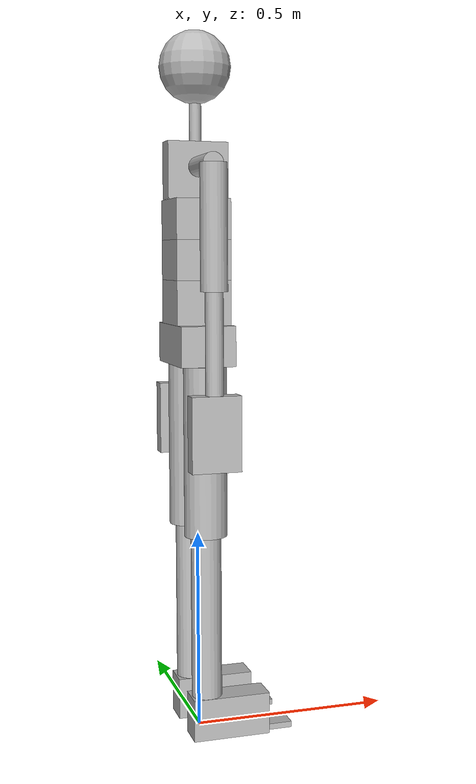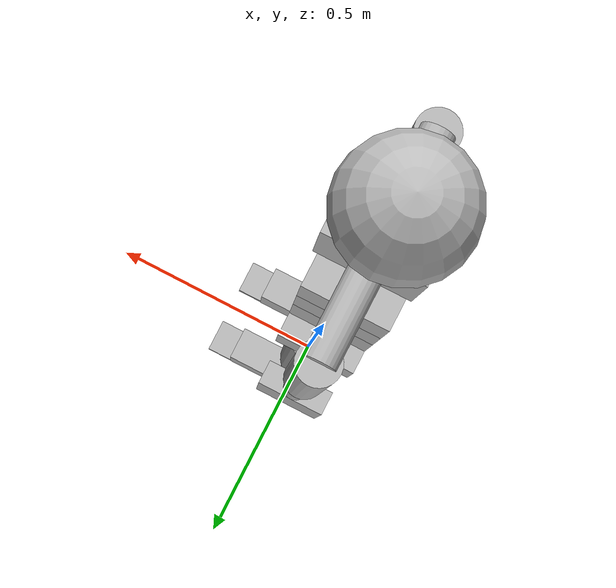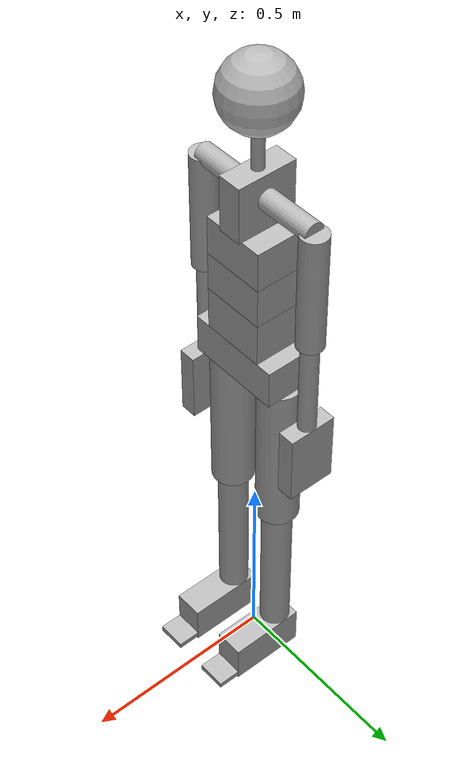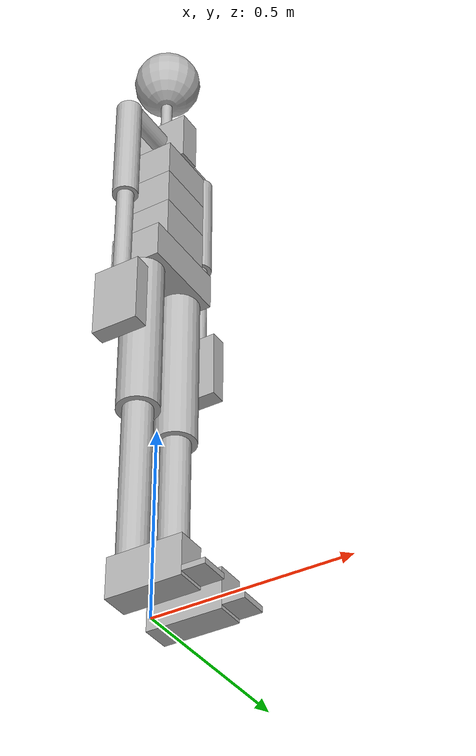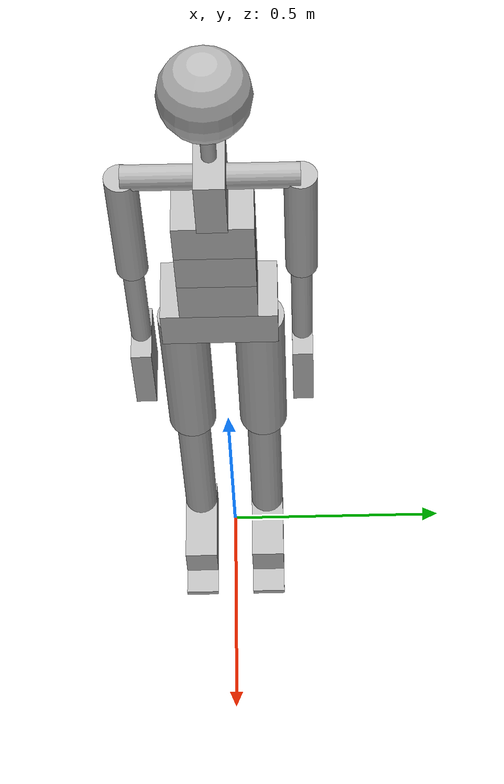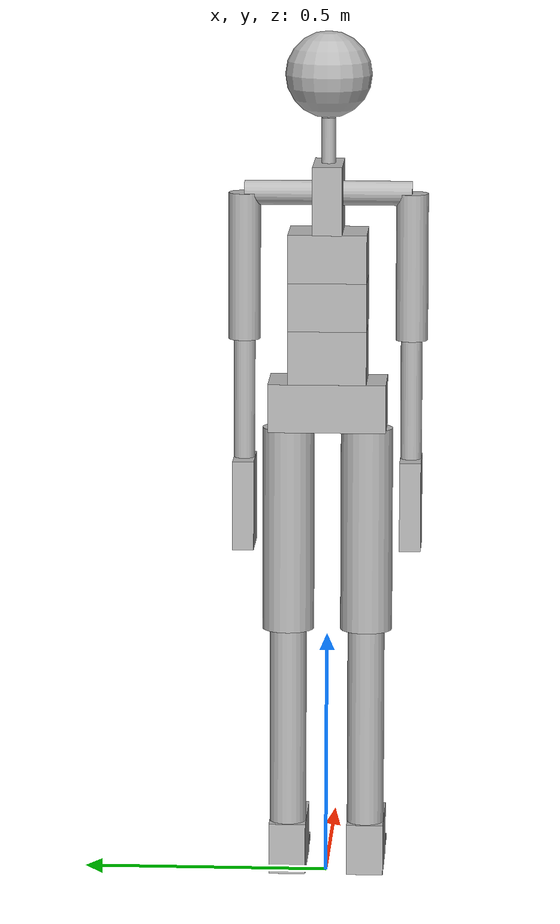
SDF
<sdf version='1.6'>
  <model name='sub0'>
    <pose>0 0 0.9325 0 0 0</pose>
    <link name='Pelvis'>
      <pose frame=''>0 0 0 0 -0 0</pose>
      <inertial>
        <pose frame=''>0 0 0.049333 0 -0 0</pose>
        <mass>4.9968</mass>
        <inertia>
          <ixx>0.028067</ixx>
          <ixy>0</ixy>
          <ixz>0</ixz>
          <iyy>0.011715</iyy>
          <iyz>0</iyz>
          <izz>0.031651</izz>
        </inertia>
      </inertial>
      <collision name='Pelvis_collision'>
        <pose frame=''>0 0 0.049333 0 -0 0</pose>
        <geometry>
          <box>
            <size>0.13554 0.24008 0.098815</size>
          </box>
        </geometry>
      </collision>
      <visual name='Pelvis_visual'>
        <pose frame=''>0 0 0.049333 0 -0 0</pose>
        <geometry>
          <box>
            <size>0.13554 0.24008 0.098815</size>
          </box>
        </geometry>
      </visual>
    </link>
    <link name='L5_f1'>
      <pose frame=''>1.5e-05 0 0.098741 0 -0 0</pose>
      <inertial>
        <pose frame=''>0 0 0 0 -0 0</pose>
        <mass>1</mass>
        <inertia>
          <ixx>0.0003</ixx>
          <ixy>0</ixy>
          <ixz>0</ixz>
          <iyy>0.0003</iyy>
          <iyz>0</iyz>
          <izz>0.0003</izz>
        </inertia>
      </inertial>
    </link>
    <joint name='jL5S1_rotx' type='revolute'>
      <child>L5_f1</child>
      <parent>Pelvis</parent>
      <axis>
        <xyz>1 0 0</xyz>
        <limit>
          <lower>-1.57</lower>
          <upper>1.57</upper>
          <effort>30</effort>
          <velocity>1</velocity>
        </limit>
        <dynamics>
          <damping>0.25</damping>
          <friction>0</friction>
          <spring_reference>0</spring_reference>
          <spring_stiffness>0</spring_stiffness>
        </dynamics>
        <use_parent_model_frame>1</use_parent_model_frame>
      </axis>
    </joint>
    <link name='L5_f2'>
      <pose frame=''>1.5e-05 0 0.098741 0 -0 0</pose>
      <inertial>
        <pose frame=''>0 0 0 0 -0 0</pose>
        <mass>1</mass>
        <inertia>
          <ixx>0.0003</ixx>
          <ixy>0</ixy>
          <ixz>0</ixz>
          <iyy>0.0003</iyy>
          <iyz>0</iyz>
          <izz>0.0003</izz>
        </inertia>
      </inertial>
    </link>
    <joint name='jL5S1_roty' type='revolute'>
      <child>L5_f2</child>
      <parent>L5_f1</parent>
      <axis>
        <xyz>0 1 0</xyz>
        <limit>
          <lower>-1.57</lower>
          <upper>1.57</upper>
          <effort>30</effort>
          <velocity>1</velocity>
        </limit>
        <dynamics>
          <damping>0.25</damping>
          <friction>0</friction>
          <spring_reference>0</spring_reference>
          <spring_stiffness>0</spring_stiffness>
        </dynamics>
        <use_parent_model_frame>1</use_parent_model_frame>
      </axis>
    </joint>
    <link name='L5'>
      <pose frame=''>1.5e-05 0 0.098741 0 -0 0</pose>
      <inertial>
        <pose frame=''>0 0 0.054602 0 -0 0</pose>
        <mass>6.3709</mass>
        <inertia>
          <ixx>0.047176</ixx>
          <ixy>0</ixy>
          <ixz>0</ixz>
          <iyy>0.03559</iyy>
          <iyz>0</iyz>
          <izz>0.069139</izz>
        </inertia>
      </inertial>
      <collision name='L5_collision'>
        <pose frame=''>0 0 0.054602 0 -0 0</pose>
        <geometry>
          <box>
            <size>0.13554 0.16014 0.1092</size>
          </box>
        </geometry>
      </collision>
      <visual name='L5_visual'>
        <pose frame=''>0 0 0.054602 0 -0 0</pose>
        <geometry>
          <box>
            <size>0.13554 0.16014 0.1092</size>
          </box>
        </geometry>
      </visual>
    </link>
    <joint name='jL5S1_rotz' type='revolute'>
      <child>L5</child>
      <parent>L5_f2</parent>
      <axis>
        <xyz>0 0 1</xyz>
        <limit>
          <lower>-1.57</lower>
          <upper>1.57</upper>
          <effort>30</effort>
          <velocity>1</velocity>
        </limit>
        <dynamics>
          <damping>0.25</damping>
          <friction>0</friction>
          <spring_reference>0</spring_reference>
          <spring_stiffness>0</spring_stiffness>
        </dynamics>
        <use_parent_model_frame>1</use_parent_model_frame>
      </axis>
    </joint>
    <link name='L3_f1'>
      <pose frame=''>-1.2e-05 0 0.207941 0 -0 0</pose>
      <inertial>
        <pose frame=''>0 0 0 0 -0 0</pose>
        <mass>1</mass>
        <inertia>
          <ixx>0.0003</ixx>
          <ixy>0</ixy>
          <ixz>0</ixz>
          <iyy>0.0003</iyy>
          <iyz>0</iyz>
          <izz>0.0003</izz>
        </inertia>
      </inertial>
    </link>
    <joint name='jL4L3_rotx' type='revolute'>
      <child>L3_f1</child>
      <parent>L5</parent>
      <axis>
        <xyz>1 0 0</xyz>
        <limit>
          <lower>-0</lower>
          <upper>0</upper>
          <effort>30</effort>
          <velocity>1</velocity>
        </limit>
        <dynamics>
          <damping>0.25</damping>
          <friction>0</friction>
          <spring_reference>0</spring_reference>
          <spring_stiffness>0</spring_stiffness>
        </dynamics>
        <use_parent_model_frame>1</use_parent_model_frame>
      </axis>
    </joint>
    <link name='L3_f2'>
      <pose frame=''>-1.2e-05 0 0.207941 0 -0 0</pose>
      <inertial>
        <pose frame=''>0 0 0 0 -0 0</pose>
        <mass>1</mass>
        <inertia>
          <ixx>0.0003</ixx>
          <ixy>0</ixy>
          <ixz>0</ixz>
          <iyy>0.0003</iyy>
          <iyz>0</iyz>
          <izz>0.0003</izz>
        </inertia>
      </inertial>
    </link>
    <joint name='jL4L3_roty' type='revolute'>
      <child>L3_f2</child>
      <parent>L3_f1</parent>
      <axis>
        <xyz>0 1 0</xyz>
        <limit>
          <lower>-0</lower>
          <upper>0</upper>
          <effort>30</effort>
          <velocity>1</velocity>
        </limit>
        <dynamics>
          <damping>0.25</damping>
          <friction>0</friction>
          <spring_reference>0</spring_reference>
          <spring_stiffness>0</spring_stiffness>
        </dynamics>
        <use_parent_model_frame>1</use_parent_model_frame>
      </axis>
    </joint>
    <link name='L3'>
      <pose frame=''>-1.2e-05 0 0.207941 0 -0 0</pose>
      <inertial>
        <pose frame=''>0 0 0.049336 0 -0 0</pose>
        <mass>6.3709</mass>
        <inertia>
          <ixx>0.046013</ixx>
          <ixy>0</ixy>
          <ixz>0</ixz>
          <iyy>0.034427</iyy>
          <iyz>0</iyz>
          <izz>0.069139</izz>
        </inertia>
      </inertial>
      <collision name='L3_collision'>
        <pose frame=''>0 0 0.049336 0 -0 0</pose>
        <geometry>
          <box>
            <size>0.13554 0.16014 0.098672</size>
          </box>
        </geometry>
      </collision>
      <visual name='L3_visual'>
        <pose frame=''>0 0 0.049336 0 -0 0</pose>
        <geometry>
          <box>
            <size>0.13554 0.16014 0.098672</size>
          </box>
        </geometry>
      </visual>
    </link>
    <joint name='jL4L3_rotz' type='revolute'>
      <child>L3</child>
      <parent>L3_f2</parent>
      <axis>
        <xyz>0 0 1</xyz>
        <limit>
          <lower>-0</lower>
          <upper>0</upper>
          <effort>30</effort>
          <velocity>1</velocity>
        </limit>
        <dynamics>
          <damping>0.25</damping>
          <friction>0</friction>
          <spring_reference>0</spring_reference>
          <spring_stiffness>0</spring_stiffness>
        </dynamics>
        <use_parent_model_frame>1</use_parent_model_frame>
      </axis>
    </joint>
    <link name='T12_f1'>
      <pose frame=''>-1.2e-05 0 0.306613 0 -0 0</pose>
      <inertial>
        <pose frame=''>0 0 0 0 -0 0</pose>
        <mass>1</mass>
        <inertia>
          <ixx>0.0003</ixx>
          <ixy>0</ixy>
          <ixz>0</ixz>
          <iyy>0.0003</iyy>
          <iyz>0</iyz>
          <izz>0.0003</izz>
        </inertia>
      </inertial>
    </link>
    <joint name='jL1T12_rotx' type='revolute'>
      <child>T12_f1</child>
      <parent>L3</parent>
      <axis>
        <xyz>1 0 0</xyz>
        <limit>
          <lower>-0</lower>
          <upper>0</upper>
          <effort>30</effort>
          <velocity>1</velocity>
        </limit>
        <dynamics>
          <damping>0.25</damping>
          <friction>0</friction>
          <spring_reference>0</spring_reference>
          <spring_stiffness>0</spring_stiffness>
        </dynamics>
        <use_parent_model_frame>1</use_parent_model_frame>
      </axis>
    </joint>
    <link name='T12_f2'>
      <pose frame=''>-1.2e-05 0 0.306613 0 -0 0</pose>
      <inertial>
        <pose frame=''>0 0 0 0 -0 0</pose>
        <mass>1</mass>
        <inertia>
          <ixx>0.0003</ixx>
          <ixy>0</ixy>
          <ixz>0</ixz>
          <iyy>0.0003</iyy>
          <iyz>0</iyz>
          <izz>0.0003</izz>
        </inertia>
      </inertial>
    </link>
    <joint name='jL1T12_roty' type='revolute'>
      <child>T12_f2</child>
      <parent>T12_f1</parent>
      <axis>
        <xyz>0 1 0</xyz>
        <limit>
          <lower>-0</lower>
          <upper>0</upper>
          <effort>30</effort>
          <velocity>1</velocity>
        </limit>
        <dynamics>
          <damping>0.25</damping>
          <friction>0</friction>
          <spring_reference>0</spring_reference>
          <spring_stiffness>0</spring_stiffness>
        </dynamics>
        <use_parent_model_frame>1</use_parent_model_frame>
      </axis>
    </joint>
    <link name='T12'>
      <pose frame=''>-1.2e-05 0 0.306613 0 -0 0</pose>
      <inertial>
        <pose frame=''>0 0 0.049336 0 -0 0</pose>
        <mass>6.3709</mass>
        <inertia>
          <ixx>0.046013</ixx>
          <ixy>0</ixy>
          <ixz>0</ixz>
          <iyy>0.034427</iyy>
          <iyz>0</iyz>
          <izz>0.069139</izz>
        </inertia>
      </inertial>
      <collision name='T12_collision'>
        <pose frame=''>0 0 0.049336 0 -0 0</pose>
        <geometry>
          <box>
            <size>0.13554 0.16014 0.098672</size>
          </box>
        </geometry>
      </collision>
      <visual name='T12_visual'>
        <pose frame=''>0 0 0.049336 0 -0 0</pose>
        <geometry>
          <box>
            <size>0.13554 0.16014 0.098672</size>
          </box>
        </geometry>
      </visual>
    </link>
    <joint name='jL1T12_rotz' type='revolute'>
      <child>T12</child>
      <parent>T12_f2</parent>
      <axis>
        <xyz>0 0 1</xyz>
        <limit>
          <lower>-0</lower>
          <upper>0</upper>
          <effort>30</effort>
          <velocity>1</velocity>
        </limit>
        <dynamics>
          <damping>0.25</damping>
          <friction>0</friction>
          <spring_reference>0</spring_reference>
          <spring_stiffness>0</spring_stiffness>
        </dynamics>
        <use_parent_model_frame>1</use_parent_model_frame>
      </axis>
    </joint>
    <link name='T8_f1'>
      <pose frame=''>-1.2e-05 0 0.405285 0 -0 0</pose>
      <inertial>
        <pose frame=''>0 0 0 0 -0 0</pose>
        <mass>1</mass>
        <inertia>
          <ixx>0.0003</ixx>
          <ixy>0</ixy>
          <ixz>0</ixz>
          <iyy>0.0003</iyy>
          <iyz>0</iyz>
          <izz>0.0003</izz>
        </inertia>
      </inertial>
    </link>
    <joint name='jT9T8_rotx' type='revolute'>
      <child>T8_f1</child>
      <parent>T12</parent>
      <axis>
        <xyz>1 0 0</xyz>
        <limit>
          <lower>-0</lower>
          <upper>0</upper>
          <effort>30</effort>
          <velocity>1</velocity>
        </limit>
        <dynamics>
          <damping>0.25</damping>
          <friction>0</friction>
          <spring_reference>0</spring_reference>
          <spring_stiffness>0</spring_stiffness>
        </dynamics>
        <use_parent_model_frame>1</use_parent_model_frame>
      </axis>
    </joint>
    <link name='T8_f2'>
      <pose frame=''>-1.2e-05 0 0.405285 0 -0 0</pose>
      <inertial>
        <pose frame=''>0 0 0 0 -0 0</pose>
        <mass>1</mass>
        <inertia>
          <ixx>0.0003</ixx>
          <ixy>0</ixy>
          <ixz>0</ixz>
          <iyy>0.0003</iyy>
          <iyz>0</iyz>
          <izz>0.0003</izz>
        </inertia>
      </inertial>
    </link>
    <joint name='jT9T8_roty' type='revolute'>
      <child>T8_f2</child>
      <parent>T8_f1</parent>
      <axis>
        <xyz>0 1 0</xyz>
        <limit>
          <lower>-0.261799</lower>
          <upper>0.872665</upper>
          <effort>30</effort>
          <velocity>1</velocity>
        </limit>
        <dynamics>
          <damping>0.25</damping>
          <friction>0</friction>
          <spring_reference>0</spring_reference>
          <spring_stiffness>0</spring_stiffness>
        </dynamics>
        <use_parent_model_frame>1</use_parent_model_frame>
      </axis>
    </joint>
    <link name='T8'>
      <pose frame=''>-1.2e-05 0 0.405285 0 -0 0</pose>
      <inertial>
        <pose frame=''>0 0 0.069461 0 -0 0</pose>
        <mass>2.4984</mass>
        <inertia>
          <ixx>0.0047729</ixx>
          <ixy>0</ixy>
          <ixz>0</ixz>
          <iyy>0.0087452</iyy>
          <iyz>0</iyz>
          <izz>0.0054818</izz>
        </inertia>
      </inertial>
      <collision name='T8_collision'>
        <pose frame=''>0 0 0.069461 0 -0 0</pose>
        <geometry>
          <box>
            <size>0.15068 0.06021 0.13892</size>
          </box>
        </geometry>
      </collision>
      <visual name='T8_visual'>
        <pose frame=''>0 0 0.069461 0 -0 0</pose>
        <geometry>
          <box>
            <size>0.15068 0.06021 0.13892</size>
          </box>
        </geometry>
      </visual>
    </link>
    <joint name='jT9T8_rotz' type='revolute'>
      <child>T8</child>
      <parent>T8_f2</parent>
      <axis>
        <xyz>0 0 1</xyz>
        <limit>
          <lower>-0.610865</lower>
          <upper>0.610865</upper>
          <effort>30</effort>
          <velocity>1</velocity>
        </limit>
        <dynamics>
          <damping>0.25</damping>
          <friction>0</friction>
          <spring_reference>0</spring_reference>
          <spring_stiffness>0</spring_stiffness>
        </dynamics>
        <use_parent_model_frame>1</use_parent_model_frame>
      </axis>
    </joint>
    <link name='LeftShoulder_f1'>
      <pose frame=''>-1.2e-05 0.030105 0.482782 0 -0 0</pose>
      <inertial>
        <pose frame=''>0 0 0 0 -0 0</pose>
        <mass>1</mass>
        <inertia>
          <ixx>0.0003</ixx>
          <ixy>0</ixy>
          <ixz>0</ixz>
          <iyy>0.0003</iyy>
          <iyz>0</iyz>
          <izz>0.0003</izz>
        </inertia>
      </inertial>
    </link>
    <joint name='jLeftC7Shoulder_rotx' type='revolute'>
      <child>LeftShoulder_f1</child>
      <parent>T8</parent>
      <axis>
        <xyz>1 0 0</xyz>
        <limit>
          <lower>-0</lower>
          <upper>0</upper>
          <effort>30</effort>
          <velocity>1</velocity>
        </limit>
        <dynamics>
          <damping>0.25</damping>
          <friction>0</friction>
          <spring_reference>0</spring_reference>
          <spring_stiffness>0</spring_stiffness>
        </dynamics>
        <use_parent_model_frame>1</use_parent_model_frame>
      </axis>
    </joint>
    <link name='LeftShoulder_f2'>
      <pose frame=''>-1.2e-05 0.030105 0.482782 0 -0 0</pose>
      <inertial>
        <pose frame=''>0 0 0 0 -0 0</pose>
        <mass>1</mass>
        <inertia>
          <ixx>0.0003</ixx>
          <ixy>0</ixy>
          <ixz>0</ixz>
          <iyy>0.0003</iyy>
          <iyz>0</iyz>
          <izz>0.0003</izz>
        </inertia>
      </inertial>
    </link>
    <joint name='jLeftC7Shoulder_roty' type='revolute'>
      <child>LeftShoulder_f2</child>
      <parent>LeftShoulder_f1</parent>
      <axis>
        <xyz>0 1 0</xyz>
        <limit>
          <lower>-0</lower>
          <upper>0</upper>
          <effort>30</effort>
          <velocity>1</velocity>
        </limit>
        <dynamics>
          <damping>0.25</damping>
          <friction>0</friction>
          <spring_reference>0</spring_reference>
          <spring_stiffness>0</spring_stiffness>
        </dynamics>
        <use_parent_model_frame>1</use_parent_model_frame>
      </axis>
    </joint>
    <link name='LeftShoulder'>
      <pose frame=''>-1.2e-05 0.030105 0.482782 0 -0 0</pose>
      <inertial>
        <pose frame=''>0 0.069978 0 0 -0 0</pose>
        <mass>1.9363</mass>
        <inertia>
          <ixx>0.0034631</ixx>
          <ixy>0</ixy>
          <ixz>0</ixz>
          <iyy>0.00060506</iyy>
          <iyz>0</iyz>
          <izz>0.0034631</izz>
        </inertia>
      </inertial>
      <collision name='LeftShoulder_collision'>
        <pose frame=''>0 0.069978 0 1.5708 -0 0</pose>
        <geometry>
          <cylinder>
            <length>0.13996</length>
            <radius>0.025</radius>
          </cylinder>
        </geometry>
      </collision>
      <visual name='LeftShoulder_visual'>
        <pose frame=''>0 0.069978 0 1.5708 -0 0</pose>
        <geometry>
          <cylinder>
            <length>0.13996</length>
            <radius>0.025</radius>
          </cylinder>
        </geometry>
      </visual>
    </link>
    <joint name='jLeftC7Shoulder_rotz' type='revolute'>
      <child>LeftShoulder</child>
      <parent>LeftShoulder_f2</parent>
      <axis>
        <xyz>0 0 1</xyz>
        <limit>
          <lower>-0.0872665</lower>
          <upper>0.785398</upper>
          <effort>30</effort>
          <velocity>1</velocity>
        </limit>
        <dynamics>
          <damping>0.25</damping>
          <friction>0</friction>
          <spring_reference>0</spring_reference>
          <spring_stiffness>0</spring_stiffness>
        </dynamics>
        <use_parent_model_frame>1</use_parent_model_frame>
      </axis>
    </joint>
    <link name='LeftUpperArm_f1'>
      <pose frame=''>-1.2e-05 0.170065 0.482782 -1.57 -0 0</pose>
      <inertial>
        <pose frame=''>0 0 0 0 -0 0</pose>
        <mass>1</mass>
        <inertia>
          <ixx>0.0003</ixx>
          <ixy>0</ixy>
          <ixz>0</ixz>
          <iyy>0.0003</iyy>
          <iyz>0</iyz>
          <izz>0.0003</izz>
        </inertia>
      </inertial>
    </link>
    <joint name='jLeftShoulder_rotx' type='revolute'>
      <child>LeftUpperArm_f1</child>
      <parent>LeftShoulder</parent>
      <axis>
        <xyz>1 0 0</xyz>
        <limit>
          <lower>-1.5708</lower>
          <upper>2.35619</upper>
          <effort>30</effort>
          <velocity>1</velocity>
        </limit>
        <dynamics>
          <damping>0.25</damping>
          <friction>0</friction>
          <spring_reference>0</spring_reference>
          <spring_stiffness>0</spring_stiffness>
        </dynamics>
        <use_parent_model_frame>1</use_parent_model_frame>
      </axis>
    </joint>
    <link name='LeftUpperArm_f2'>
      <pose frame=''>-1.2e-05 0.170065 0.482782 -1.57 -0 0</pose>
      <inertial>
        <pose frame=''>0 0 0 0 -0 0</pose>
        <mass>1</mass>
        <inertia>
          <ixx>0.0003</ixx>
          <ixy>0</ixy>
          <ixz>0</ixz>
          <iyy>0.0003</iyy>
          <iyz>0</iyz>
          <izz>0.0003</izz>
        </inertia>
      </inertial>
    </link>
    <joint name='jLeftShoulder_roty' type='revolute'>
      <child>LeftUpperArm_f2</child>
      <parent>LeftUpperArm_f1</parent>
      <axis>
        <xyz>0 1 0</xyz>
        <limit>
          <lower>-1.5708</lower>
          <upper>1.5708</upper>
          <effort>30</effort>
          <velocity>1</velocity>
        </limit>
        <dynamics>
          <damping>0.25</damping>
          <friction>0</friction>
          <spring_reference>0</spring_reference>
          <spring_stiffness>0</spring_stiffness>
        </dynamics>
        <use_parent_model_frame>1</use_parent_model_frame>
      </axis>
    </joint>
    <link name='LeftUpperArm'>
      <pose frame=''>-1.2e-05 0.170065 0.482782 -1.57 -0 0</pose>
      <inertial>
        <pose frame=''>0 0.15002 0 0 -0 0</pose>
        <mass>1.8738</mass>
        <inertia>
          <ixx>0.014553</ixx>
          <ixy>0</ixy>
          <ixz>0</ixz>
          <iyy>0.00099006</iyy>
          <iyz>0</iyz>
          <izz>0.014553</izz>
        </inertia>
      </inertial>
      <collision name='LeftUpperArm_collision'>
        <pose frame=''>0 0.15002 0 1.5708 -0 0</pose>
        <geometry>
          <cylinder>
            <length>0.30005</length>
            <radius>0.032507</radius>
          </cylinder>
        </geometry>
      </collision>
      <visual name='LeftUpperArm_visual'>
        <pose frame=''>0 0.15002 0 1.5708 -0 0</pose>
        <geometry>
          <cylinder>
            <length>0.30005</length>
            <radius>0.032507</radius>
          </cylinder>
        </geometry>
      </visual>
    </link>
    <joint name='jLeftShoulder_rotz' type='revolute'>
      <child>LeftUpperArm</child>
      <parent>LeftUpperArm_f2</parent>
      <axis>
        <xyz>0 0 1</xyz>
        <limit>
          <lower>-3.14159</lower>
          <upper>0.785398</upper>
          <effort>30</effort>
          <velocity>1</velocity>
        </limit>
        <dynamics>
          <damping>0.25</damping>
          <friction>0</friction>
          <spring_reference>0</spring_reference>
          <spring_stiffness>0</spring_stiffness>
        </dynamics>
        <use_parent_model_frame>1</use_parent_model_frame>
      </axis>
    </joint>
    <link name='LeftForeArm_f1'>
      <pose frame=''>-1.2e-05 0.170065 0.182732 -1.57 -0 0</pose>
      <inertial>
        <pose frame=''>0 0 0 0 -0 0</pose>
        <mass>1</mass>
        <inertia>
          <ixx>0.0003</ixx>
          <ixy>0</ixy>
          <ixz>0</ixz>
          <iyy>0.0003</iyy>
          <iyz>0</iyz>
          <izz>0.0003</izz>
        </inertia>
      </inertial>
    </link>
    <joint name='jLeftElbow_rotx' type='revolute'>
      <child>LeftForeArm_f1</child>
      <parent>LeftUpperArm</parent>
      <axis>
        <xyz>1 0 0</xyz>
        <limit>
          <lower>-0.174533</lower>
          <upper>0.174533</upper>
          <effort>30</effort>
          <velocity>1</velocity>
        </limit>
        <dynamics>
          <damping>0.25</damping>
          <friction>0</friction>
          <spring_reference>0</spring_reference>
          <spring_stiffness>0</spring_stiffness>
        </dynamics>
        <use_parent_model_frame>1</use_parent_model_frame>
      </axis>
    </joint>
    <link name='LeftForeArm_f2'>
      <pose frame=''>-1.2e-05 0.170065 0.182732 -1.57 -0 0</pose>
      <inertial>
        <pose frame=''>0 0 0 0 -0 0</pose>
        <mass>1</mass>
        <inertia>
          <ixx>0.0003</ixx>
          <ixy>0</ixy>
          <ixz>0</ixz>
          <iyy>0.0003</iyy>
          <iyz>0</iyz>
          <izz>0.0003</izz>
        </inertia>
      </inertial>
    </link>
    <joint name='jLeftElbow_roty' type='revolute'>
      <child>LeftForeArm_f2</child>
      <parent>LeftForeArm_f1</parent>
      <axis>
        <xyz>0 1 0</xyz>
        <limit>
          <lower>-1.5708</lower>
          <upper>1.48353</upper>
          <effort>30</effort>
          <velocity>1</velocity>
        </limit>
        <dynamics>
          <damping>0.25</damping>
          <friction>0</friction>
          <spring_reference>0</spring_reference>
          <spring_stiffness>0</spring_stiffness>
        </dynamics>
        <use_parent_model_frame>1</use_parent_model_frame>
      </axis>
    </joint>
    <link name='LeftForeArm'>
      <pose frame=''>-1.2e-05 0.170065 0.182732 -1.57 -0 0</pose>
      <inertial>
        <pose frame=''>0 0.12263 0 0 -0 0</pose>
        <mass>1.2492</mass>
        <inertia>
          <ixx>0.0064089</ixx>
          <ixy>0</ixy>
          <ixz>0</ixz>
          <iyy>0.00029335</iyy>
          <iyz>0</iyz>
          <izz>0.0064089</izz>
        </inertia>
      </inertial>
      <collision name='LeftForeArm_collision'>
        <pose frame=''>0 0.12263 0 1.5708 -0 0</pose>
        <geometry>
          <cylinder>
            <length>0.24527</length>
            <radius>0.021672</radius>
          </cylinder>
        </geometry>
      </collision>
      <visual name='LeftForeArm_visual'>
        <pose frame=''>0 0.12263 0 1.5708 -0 0</pose>
        <geometry>
          <cylinder>
            <length>0.24527</length>
            <radius>0.021672</radius>
          </cylinder>
        </geometry>
      </visual>
    </link>
    <joint name='jLeftElbow_rotz' type='revolute'>
      <child>LeftForeArm</child>
      <parent>LeftForeArm_f2</parent>
      <axis>
        <xyz>0 0 1</xyz>
        <limit>
          <lower>-2.53073</lower>
          <upper>0</upper>
          <effort>30</effort>
          <velocity>1</velocity>
        </limit>
        <dynamics>
          <damping>0.25</damping>
          <friction>0</friction>
          <spring_reference>0</spring_reference>
          <spring_stiffness>0</spring_stiffness>
        </dynamics>
        <use_parent_model_frame>1</use_parent_model_frame>
      </axis>
    </joint>
    <link name='LeftHand_f1'>
      <pose frame=''>-1.1e-05 0.170065 -0.062538 -1.57 -0 0</pose>
      <inertial>
        <pose frame=''>0 0 0 0 -0 0</pose>
        <mass>1</mass>
        <inertia>
          <ixx>0.0003</ixx>
          <ixy>0</ixy>
          <ixz>0</ixz>
          <iyy>0.0003</iyy>
          <iyz>0</iyz>
          <izz>0.0003</izz>
        </inertia>
      </inertial>
    </link>
    <joint name='jLeftWrist_rotx' type='revolute'>
      <child>LeftHand_f1</child>
      <parent>LeftForeArm</parent>
      <axis>
        <xyz>1 0 0</xyz>
        <limit>
          <lower>-1.0472</lower>
          <upper>0.872665</upper>
          <effort>30</effort>
          <velocity>1</velocity>
        </limit>
        <dynamics>
          <damping>0.25</damping>
          <friction>0</friction>
          <spring_reference>0</spring_reference>
          <spring_stiffness>0</spring_stiffness>
        </dynamics>
        <use_parent_model_frame>1</use_parent_model_frame>
      </axis>
    </joint>
    <link name='LeftHand_f2'>
      <pose frame=''>-1.1e-05 0.170065 -0.062538 -1.57 -0 0</pose>
      <inertial>
        <pose frame=''>0 0 0 0 -0 0</pose>
        <mass>1</mass>
        <inertia>
          <ixx>0.0003</ixx>
          <ixy>0</ixy>
          <ixz>0</ixz>
          <iyy>0.0003</iyy>
          <iyz>0</iyz>
          <izz>0.0003</izz>
        </inertia>
      </inertial>
    </link>
    <joint name='jLeftWrist_roty' type='revolute'>
      <child>LeftHand_f2</child>
      <parent>LeftHand_f1</parent>
      <axis>
        <xyz>0 1 0</xyz>
        <limit>
          <lower>-0.174533</lower>
          <upper>0.174533</upper>
          <effort>30</effort>
          <velocity>1</velocity>
        </limit>
        <dynamics>
          <damping>0.25</damping>
          <friction>0</friction>
          <spring_reference>0</spring_reference>
          <spring_stiffness>0</spring_stiffness>
        </dynamics>
        <use_parent_model_frame>1</use_parent_model_frame>
      </axis>
    </joint>
    <link name='LeftHand'>
      <pose frame=''>-1.1e-05 0.170065 -0.062538 -1.57 -0 0</pose>
      <inertial>
        <pose frame=''>0 0.091535 0 0 -0 0</pose>
        <mass>0.37476</mass>
        <inertia>
          <ixx>0.0011053</ixx>
          <ixy>0</ixy>
          <ixz>0</ixz>
          <iyy>0.00052385</iyy>
          <iyz>0</iyz>
          <izz>0.0015118</izz>
        </inertia>
      </inertial>
      <collision name='LeftHand_collision'>
        <pose frame=''>0 0.091535 0 0 -0 0</pose>
        <geometry>
          <box>
            <size>0.12205 0.18307 0.043343</size>
          </box>
        </geometry>
      </collision>
      <visual name='LeftHand_visual'>
        <pose frame=''>0 0.091535 0 0 -0 0</pose>
        <geometry>
          <box>
            <size>0.12205 0.18307 0.043343</size>
          </box>
        </geometry>
      </visual>
    </link>
    <joint name='jLeftWrist_rotz' type='revolute'>
      <child>LeftHand</child>
      <parent>LeftHand_f2</parent>
      <axis>
        <xyz>0 0 1</xyz>
        <limit>
          <lower>-3.14</lower>
          <upper>3.14</upper>
          <effort>30</effort>
          <velocity>1</velocity>
        </limit>
        <dynamics>
          <damping>0.25</damping>
          <friction>0</friction>
          <spring_reference>0</spring_reference>
          <spring_stiffness>0</spring_stiffness>
        </dynamics>
        <use_parent_model_frame>1</use_parent_model_frame>
      </axis>
    </joint>
    <link name='RightShoulder_f1'>
      <pose frame=''>-1.2e-05 -0.030105 0.482782 0 -0 0</pose>
      <inertial>
        <pose frame=''>0 0 0 0 -0 0</pose>
        <mass>1</mass>
        <inertia>
          <ixx>0.0003</ixx>
          <ixy>0</ixy>
          <ixz>0</ixz>
          <iyy>0.0003</iyy>
          <iyz>0</iyz>
          <izz>0.0003</izz>
        </inertia>
      </inertial>
    </link>
    <joint name='jRightC7Shoulder_rotx' type='revolute'>
      <child>RightShoulder_f1</child>
      <parent>T8</parent>
      <axis>
        <xyz>1 0 0</xyz>
        <limit>
          <lower>-0</lower>
          <upper>0</upper>
          <effort>30</effort>
          <velocity>1</velocity>
        </limit>
        <dynamics>
          <damping>0.25</damping>
          <friction>0</friction>
          <spring_reference>0</spring_reference>
          <spring_stiffness>0</spring_stiffness>
        </dynamics>
        <use_parent_model_frame>1</use_parent_model_frame>
      </axis>
    </joint>
    <link name='RightShoulder_f2'>
      <pose frame=''>-1.2e-05 -0.030105 0.482782 0 -0 0</pose>
      <inertial>
        <pose frame=''>0 0 0 0 -0 0</pose>
        <mass>1</mass>
        <inertia>
          <ixx>0.0003</ixx>
          <ixy>0</ixy>
          <ixz>0</ixz>
          <iyy>0.0003</iyy>
          <iyz>0</iyz>
          <izz>0.0003</izz>
        </inertia>
      </inertial>
    </link>
    <joint name='jRightC7Shoulder_roty' type='revolute'>
      <child>RightShoulder_f2</child>
      <parent>RightShoulder_f1</parent>
      <axis>
        <xyz>0 1 0</xyz>
        <limit>
          <lower>-0</lower>
          <upper>0</upper>
          <effort>30</effort>
          <velocity>1</velocity>
        </limit>
        <dynamics>
          <damping>0.25</damping>
          <friction>0</friction>
          <spring_reference>0</spring_reference>
          <spring_stiffness>0</spring_stiffness>
        </dynamics>
        <use_parent_model_frame>1</use_parent_model_frame>
      </axis>
    </joint>
    <link name='RightShoulder'>
      <pose frame=''>-1.2e-05 -0.030105 0.482782 0 -0 0</pose>
      <inertial>
        <pose frame=''>0 -0.069978 0 0 -0 0</pose>
        <mass>1.9363</mass>
        <inertia>
          <ixx>0.0034631</ixx>
          <ixy>0</ixy>
          <ixz>0</ixz>
          <iyy>0.00060506</iyy>
          <iyz>0</iyz>
          <izz>0.0034631</izz>
        </inertia>
      </inertial>
      <collision name='RightShoulder_collision'>
        <pose frame=''>0 -0.069978 0 1.5708 -0 0</pose>
        <geometry>
          <cylinder>
            <length>0.13996</length>
            <radius>0.025</radius>
          </cylinder>
        </geometry>
      </collision>
      <visual name='RightShoulder_visual'>
        <pose frame=''>0 -0.069978 0 1.5708 -0 0</pose>
        <geometry>
          <cylinder>
            <length>0.13996</length>
            <radius>0.025</radius>
          </cylinder>
        </geometry>
      </visual>
    </link>
    <joint name='jRightC7Shoulder_rotz' type='revolute'>
      <child>RightShoulder</child>
      <parent>RightShoulder_f2</parent>
      <axis>
        <xyz>0 0 1</xyz>
        <limit>
          <lower>-0.0872665</lower>
          <upper>0.785398</upper>
          <effort>30</effort>
          <velocity>1</velocity>
        </limit>
        <dynamics>
          <damping>0.25</damping>
          <friction>0</friction>
          <spring_reference>0</spring_reference>
          <spring_stiffness>0</spring_stiffness>
        </dynamics>
        <use_parent_model_frame>1</use_parent_model_frame>
      </axis>
    </joint>
    <link name='RightUpperArm_f1'>
      <pose frame=''>-1.2e-05 -0.170065 0.482782 1.57 -0 0</pose>
      <inertial>
        <pose frame=''>0 0 0 0 -0 0</pose>
        <mass>1</mass>
        <inertia>
          <ixx>0.0003</ixx>
          <ixy>0</ixy>
          <ixz>0</ixz>
          <iyy>0.0003</iyy>
          <iyz>0</iyz>
          <izz>0.0003</izz>
        </inertia>
      </inertial>
    </link>
    <joint name='jRightShoulder_rotx' type='revolute'>
      <child>RightUpperArm_f1</child>
      <parent>RightShoulder</parent>
      <axis>
        <xyz>1 0 0</xyz>
        <limit>
          <lower>-2.35619</lower>
          <upper>1.5708</upper>
          <effort>30</effort>
          <velocity>1</velocity>
        </limit>
        <dynamics>
          <damping>0.25</damping>
          <friction>0</friction>
          <spring_reference>0</spring_reference>
          <spring_stiffness>0</spring_stiffness>
        </dynamics>
        <use_parent_model_frame>1</use_parent_model_frame>
      </axis>
    </joint>
    <link name='RightUpperArm_f2'>
      <pose frame=''>-1.2e-05 -0.170065 0.482782 1.57 -0 0</pose>
      <inertial>
        <pose frame=''>0 0 0 0 -0 0</pose>
        <mass>1</mass>
        <inertia>
          <ixx>0.0003</ixx>
          <ixy>0</ixy>
          <ixz>0</ixz>
          <iyy>0.0003</iyy>
          <iyz>0</iyz>
          <izz>0.0003</izz>
        </inertia>
      </inertial>
    </link>
    <joint name='jRightShoulder_roty' type='revolute'>
      <child>RightUpperArm_f2</child>
      <parent>RightUpperArm_f1</parent>
      <axis>
        <xyz>0 1 0</xyz>
        <limit>
          <lower>-1.5708</lower>
          <upper>1.5708</upper>
          <effort>30</effort>
          <velocity>1</velocity>
        </limit>
        <dynamics>
          <damping>0.25</damping>
          <friction>0</friction>
          <spring_reference>0</spring_reference>
          <spring_stiffness>0</spring_stiffness>
        </dynamics>
        <use_parent_model_frame>1</use_parent_model_frame>
      </axis>
    </joint>
    <link name='RightUpperArm'>
      <pose frame=''>-1.2e-05 -0.170065 0.482782 1.57 -0 0</pose>
      <inertial>
        <pose frame=''>0 -0.15002 0 0 -0 0</pose>
        <mass>1.8738</mass>
        <inertia>
          <ixx>0.014553</ixx>
          <ixy>0</ixy>
          <ixz>0</ixz>
          <iyy>0.00099006</iyy>
          <iyz>0</iyz>
          <izz>0.014553</izz>
        </inertia>
      </inertial>
      <collision name='RightUpperArm_collision'>
        <pose frame=''>0 -0.15002 0 1.5708 -0 0</pose>
        <geometry>
          <cylinder>
            <length>0.30005</length>
            <radius>0.032507</radius>
          </cylinder>
        </geometry>
      </collision>
      <visual name='RightUpperArm_visual'>
        <pose frame=''>0 -0.15002 0 1.5708 -0 0</pose>
        <geometry>
          <cylinder>
            <length>0.30005</length>
            <radius>0.032507</radius>
          </cylinder>
        </geometry>
      </visual>
    </link>
    <joint name='jRightShoulder_rotz' type='revolute'>
      <child>RightUpperArm</child>
      <parent>RightUpperArm_f2</parent>
      <axis>
        <xyz>0 0 1</xyz>
        <limit>
          <lower>-0.785398</lower>
          <upper>3.14159</upper>
          <effort>30</effort>
          <velocity>1</velocity>
        </limit>
        <dynamics>
          <damping>0.25</damping>
          <friction>0</friction>
          <spring_reference>0</spring_reference>
          <spring_stiffness>0</spring_stiffness>
        </dynamics>
        <use_parent_model_frame>1</use_parent_model_frame>
      </axis>
    </joint>
    <link name='RightForeArm_f1'>
      <pose frame=''>-1.2e-05 -0.170065 0.182732 1.57 -0 0</pose>
      <inertial>
        <pose frame=''>0 0 0 0 -0 0</pose>
        <mass>1</mass>
        <inertia>
          <ixx>0.0003</ixx>
          <ixy>0</ixy>
          <ixz>0</ixz>
          <iyy>0.0003</iyy>
          <iyz>0</iyz>
          <izz>0.0003</izz>
        </inertia>
      </inertial>
    </link>
    <joint name='jRightElbow_rotx' type='revolute'>
      <child>RightForeArm_f1</child>
      <parent>RightUpperArm</parent>
      <axis>
        <xyz>1 0 0</xyz>
        <limit>
          <lower>-0.174533</lower>
          <upper>0.174533</upper>
          <effort>30</effort>
          <velocity>1</velocity>
        </limit>
        <dynamics>
          <damping>0.25</damping>
          <friction>0</friction>
          <spring_reference>0</spring_reference>
          <spring_stiffness>0</spring_stiffness>
        </dynamics>
        <use_parent_model_frame>1</use_parent_model_frame>
      </axis>
    </joint>
    <link name='RightForeArm_f2'>
      <pose frame=''>-1.2e-05 -0.170065 0.182732 1.57 -0 0</pose>
      <inertial>
        <pose frame=''>0 0 0 0 -0 0</pose>
        <mass>1</mass>
        <inertia>
          <ixx>0.0003</ixx>
          <ixy>0</ixy>
          <ixz>0</ixz>
          <iyy>0.0003</iyy>
          <iyz>0</iyz>
          <izz>0.0003</izz>
        </inertia>
      </inertial>
    </link>
    <joint name='jRightElbow_roty' type='revolute'>
      <child>RightForeArm_f2</child>
      <parent>RightForeArm_f1</parent>
      <axis>
        <xyz>0 1 0</xyz>
        <limit>
          <lower>-1.5708</lower>
          <upper>1.48353</upper>
          <effort>30</effort>
          <velocity>1</velocity>
        </limit>
        <dynamics>
          <damping>0.25</damping>
          <friction>0</friction>
          <spring_reference>0</spring_reference>
          <spring_stiffness>0</spring_stiffness>
        </dynamics>
        <use_parent_model_frame>1</use_parent_model_frame>
      </axis>
    </joint>
    <link name='RightForeArm'>
      <pose frame=''>-1.2e-05 -0.170065 0.182732 1.57 -0 0</pose>
      <inertial>
        <pose frame=''>0 -0.12263 0 0 -0 0</pose>
        <mass>1.2492</mass>
        <inertia>
          <ixx>0.0064089</ixx>
          <ixy>0</ixy>
          <ixz>0</ixz>
          <iyy>0.00029335</iyy>
          <iyz>0</iyz>
          <izz>0.0064089</izz>
        </inertia>
      </inertial>
      <collision name='RightForeArm_collision'>
        <pose frame=''>0 -0.12263 0 1.5708 -0 0</pose>
        <geometry>
          <cylinder>
            <length>0.24527</length>
            <radius>0.021672</radius>
          </cylinder>
        </geometry>
      </collision>
      <visual name='RightForeArm_visual'>
        <pose frame=''>0 -0.12263 0 1.5708 -0 0</pose>
        <geometry>
          <cylinder>
            <length>0.24527</length>
            <radius>0.021672</radius>
          </cylinder>
        </geometry>
      </visual>
    </link>
    <joint name='jRightElbow_rotz' type='revolute'>
      <child>RightForeArm</child>
      <parent>RightForeArm_f2</parent>
      <axis>
        <xyz>0 0 1</xyz>
        <limit>
          <lower>0</lower>
          <upper>2.53073</upper>
          <effort>30</effort>
          <velocity>1</velocity>
        </limit>
        <dynamics>
          <damping>0.25</damping>
          <friction>0</friction>
          <spring_reference>0</spring_reference>
          <spring_stiffness>0</spring_stiffness>
        </dynamics>
        <use_parent_model_frame>1</use_parent_model_frame>
      </axis>
    </joint>
    <link name='RightHand_f1'>
      <pose frame=''>-1.2e-05 -0.170065 -0.062538 1.57 -0 0</pose>
      <inertial>
        <pose frame=''>0 0 0 0 -0 0</pose>
        <mass>1</mass>
        <inertia>
          <ixx>0.0003</ixx>
          <ixy>0</ixy>
          <ixz>0</ixz>
          <iyy>0.0003</iyy>
          <iyz>0</iyz>
          <izz>0.0003</izz>
        </inertia>
      </inertial>
    </link>
    <joint name='jRightWrist_rotx' type='revolute'>
      <child>RightHand_f1</child>
      <parent>RightForeArm</parent>
      <axis>
        <xyz>1 0 0</xyz>
        <limit>
          <lower>-0.872665</lower>
          <upper>1.0472</upper>
          <effort>30</effort>
          <velocity>1</velocity>
        </limit>
        <dynamics>
          <damping>0.25</damping>
          <friction>0</friction>
          <spring_reference>0</spring_reference>
          <spring_stiffness>0</spring_stiffness>
        </dynamics>
        <use_parent_model_frame>1</use_parent_model_frame>
      </axis>
    </joint>
    <link name='RightHand_f2'>
      <pose frame=''>-1.2e-05 -0.170065 -0.062538 1.57 -0 0</pose>
      <inertial>
        <pose frame=''>0 0 0 0 -0 0</pose>
        <mass>1</mass>
        <inertia>
          <ixx>0.0003</ixx>
          <ixy>0</ixy>
          <ixz>0</ixz>
          <iyy>0.0003</iyy>
          <iyz>0</iyz>
          <izz>0.0003</izz>
        </inertia>
      </inertial>
    </link>
    <joint name='jRightWrist_roty' type='revolute'>
      <child>RightHand_f2</child>
      <parent>RightHand_f1</parent>
      <axis>
        <xyz>0 1 0</xyz>
        <limit>
          <lower>-0.174533</lower>
          <upper>0.174533</upper>
          <effort>30</effort>
          <velocity>1</velocity>
        </limit>
        <dynamics>
          <damping>0.25</damping>
          <friction>0</friction>
          <spring_reference>0</spring_reference>
          <spring_stiffness>0</spring_stiffness>
        </dynamics>
        <use_parent_model_frame>1</use_parent_model_frame>
      </axis>
    </joint>
    <link name='RightHand'>
      <pose frame=''>-1.2e-05 -0.170065 -0.062538 1.57 -0 0</pose>
      <inertial>
        <pose frame=''>0 -0.091535 0 0 -0 0</pose>
        <mass>0.37476</mass>
        <inertia>
          <ixx>0.0011053</ixx>
          <ixy>0</ixy>
          <ixz>0</ixz>
          <iyy>0.00052385</iyy>
          <iyz>0</iyz>
          <izz>0.0015118</izz>
        </inertia>
      </inertial>
      <collision name='RightHand_collision'>
        <pose frame=''>0 -0.091535 0 0 -0 0</pose>
        <geometry>
          <box>
            <size>0.12205 0.18307 0.043343</size>
          </box>
        </geometry>
      </collision>
      <visual name='RightHand_visual'>
        <pose frame=''>0 -0.091535 0 0 -0 0</pose>
        <geometry>
          <box>
            <size>0.12205 0.18307 0.043343</size>
          </box>
        </geometry>
      </visual>
    </link>
    <joint name='jRightWrist_rotz' type='revolute'>
      <child>RightHand</child>
      <parent>RightHand_f2</parent>
      <axis>
        <xyz>0 0 1</xyz>
        <limit>
          <lower>-3.14</lower>
          <upper>3.14</upper>
          <effort>30</effort>
          <velocity>1</velocity>
        </limit>
        <dynamics>
          <damping>0.25</damping>
          <friction>0</friction>
          <spring_reference>0</spring_reference>
          <spring_stiffness>0</spring_stiffness>
        </dynamics>
        <use_parent_model_frame>1</use_parent_model_frame>
      </axis>
    </joint>
    <link name='Neck_f1'>
      <pose frame=''>-1.2e-05 0 0.544205 0 -0 0</pose>
      <inertial>
        <pose frame=''>0 0 0 0 -0 0</pose>
        <mass>1</mass>
        <inertia>
          <ixx>0.0003</ixx>
          <ixy>0</ixy>
          <ixz>0</ixz>
          <iyy>0.0003</iyy>
          <iyz>0</iyz>
          <izz>0.0003</izz>
        </inertia>
      </inertial>
    </link>
    <joint name='jT1C7_rotx' type='revolute'>
      <child>Neck_f1</child>
      <parent>T8</parent>
      <axis>
        <xyz>1 0 0</xyz>
        <limit>
          <lower>-0.174533</lower>
          <upper>0.174533</upper>
          <effort>30</effort>
          <velocity>1</velocity>
        </limit>
        <dynamics>
          <damping>0.25</damping>
          <friction>0</friction>
          <spring_reference>0</spring_reference>
          <spring_stiffness>0</spring_stiffness>
        </dynamics>
        <use_parent_model_frame>1</use_parent_model_frame>
      </axis>
    </joint>
    <link name='Neck_f2'>
      <pose frame=''>-1.2e-05 0 0.544205 0 -0 0</pose>
      <inertial>
        <pose frame=''>0 0 0 0 -0 0</pose>
        <mass>1</mass>
        <inertia>
          <ixx>0.0003</ixx>
          <ixy>0</ixy>
          <ixz>0</ixz>
          <iyy>0.0003</iyy>
          <iyz>0</iyz>
          <izz>0.0003</izz>
        </inertia>
      </inertial>
    </link>
    <joint name='jT1C7_roty' type='revolute'>
      <child>Neck_f2</child>
      <parent>Neck_f1</parent>
      <axis>
        <xyz>0 1 0</xyz>
        <limit>
          <lower>-0.174533</lower>
          <upper>0.174533</upper>
          <effort>30</effort>
          <velocity>1</velocity>
        </limit>
        <dynamics>
          <damping>0.25</damping>
          <friction>0</friction>
          <spring_reference>0</spring_reference>
          <spring_stiffness>0</spring_stiffness>
        </dynamics>
        <use_parent_model_frame>1</use_parent_model_frame>
      </axis>
    </joint>
    <link name='Neck'>
      <pose frame=''>-1.2e-05 0 0.544205 0 -0 0</pose>
      <inertial>
        <pose frame=''>0 0 0.045917 0 -0 0</pose>
        <mass>0.74952</mass>
        <inertia>
          <ixx>0.0006888</ixx>
          <ixy>0</ixy>
          <ixz>0</ixz>
          <iyy>0.0006888</iyy>
          <iyz>0</iyz>
          <izz>0.00032408</izz>
        </inertia>
      </inertial>
      <collision name='Neck_collision'>
        <pose frame=''>0 0 0.045917 0 -0 0</pose>
        <geometry>
          <cylinder>
            <length>0.091834</length>
            <radius>0.014704</radius>
          </cylinder>
        </geometry>
      </collision>
      <visual name='Neck_visual'>
        <pose frame=''>0 0 0.045917 0 -0 0</pose>
        <geometry>
          <cylinder>
            <length>0.091834</length>
            <radius>0.014704</radius>
          </cylinder>
        </geometry>
      </visual>
    </link>
    <joint name='jT1C7_rotz' type='revolute'>
      <child>Neck</child>
      <parent>Neck_f2</parent>
      <axis>
        <xyz>0 0 1</xyz>
        <limit>
          <lower>-0.174533</lower>
          <upper>0.174533</upper>
          <effort>30</effort>
          <velocity>1</velocity>
        </limit>
        <dynamics>
          <damping>0.25</damping>
          <friction>0</friction>
          <spring_reference>0</spring_reference>
          <spring_stiffness>0</spring_stiffness>
        </dynamics>
        <use_parent_model_frame>1</use_parent_model_frame>
      </axis>
    </joint>
    <link name='Head_f1'>
      <pose frame=''>-7.7e-05 0 0.636039 0 -0 0</pose>
      <inertial>
        <pose frame=''>0 0 0 0 -0 0</pose>
        <mass>1</mass>
        <inertia>
          <ixx>0.0003</ixx>
          <ixy>0</ixy>
          <ixz>0</ixz>
          <iyy>0.0003</iyy>
          <iyz>0</iyz>
          <izz>0.0003</izz>
        </inertia>
      </inertial>
    </link>
    <joint name='jC1Head_rotx' type='revolute'>
      <child>Head_f1</child>
      <parent>Neck</parent>
      <axis>
        <xyz>1 0 0</xyz>
        <limit>
          <lower>-0.174533</lower>
          <upper>0.174533</upper>
          <effort>30</effort>
          <velocity>1</velocity>
        </limit>
        <dynamics>
          <damping>0.25</damping>
          <friction>0</friction>
          <spring_reference>0</spring_reference>
          <spring_stiffness>0</spring_stiffness>
        </dynamics>
        <use_parent_model_frame>1</use_parent_model_frame>
      </axis>
    </joint>
    <link name='Head_f2'>
      <pose frame=''>-7.7e-05 0 0.636039 0 -0 0</pose>
      <inertial>
        <pose frame=''>0 0 0 0 -0 0</pose>
        <mass>1</mass>
        <inertia>
          <ixx>0.0003</ixx>
          <ixy>0</ixy>
          <ixz>0</ixz>
          <iyy>0.0003</iyy>
          <iyz>0</iyz>
          <izz>0.0003</izz>
        </inertia>
      </inertial>
    </link>
    <joint name='jC1Head_roty' type='revolute'>
      <child>Head_f2</child>
      <parent>Head_f1</parent>
      <axis>
        <xyz>0 1 0</xyz>
        <limit>
          <lower>-0.174533</lower>
          <upper>0.174533</upper>
          <effort>30</effort>
          <velocity>1</velocity>
        </limit>
        <dynamics>
          <damping>0.25</damping>
          <friction>0</friction>
          <spring_reference>0</spring_reference>
          <spring_stiffness>0</spring_stiffness>
        </dynamics>
        <use_parent_model_frame>1</use_parent_model_frame>
      </axis>
    </joint>
    <link name='Head'>
      <pose frame=''>-7.7e-05 0 0.636039 0 -0 0</pose>
      <inertial>
        <pose frame=''>0 0 0.087994 0 -0 0</pose>
        <mass>2.2486</mass>
        <inertia>
          <ixx>0.0069641</ixx>
          <ixy>0</ixy>
          <ixz>0</ixz>
          <iyy>0.0069641</iyy>
          <iyz>0</iyz>
          <izz>0.0069641</izz>
        </inertia>
      </inertial>
      <collision name='Head_collision'>
        <pose frame=''>0 0 0.087994 0 -0 0</pose>
        <geometry>
          <sphere>
            <radius>0.087994</radius>
          </sphere>
        </geometry>
      </collision>
      <visual name='Head_visual'>
        <pose frame=''>0 0 0.087994 0 -0 0</pose>
        <geometry>
          <sphere>
            <radius>0.087994</radius>
          </sphere>
        </geometry>
      </visual>
    </link>
    <joint name='jC1Head_rotz' type='revolute'>
      <child>Head</child>
      <parent>Head_f2</parent>
      <axis>
        <xyz>0 0 1</xyz>
        <limit>
          <lower>-0.174533</lower>
          <upper>0.174533</upper>
          <effort>30</effort>
          <velocity>1</velocity>
        </limit>
        <dynamics>
          <damping>0.25</damping>
          <friction>0</friction>
          <spring_reference>0</spring_reference>
          <spring_stiffness>0</spring_stiffness>
        </dynamics>
        <use_parent_model_frame>1</use_parent_model_frame>
      </axis>
    </joint>
    <link name='LeftUpperLeg_f1'>
      <pose frame=''>-8e-06 0.080069 -7.4e-05 0 -0 0</pose>
      <inertial>
        <pose frame=''>0 0 0 0 -0 0</pose>
        <mass>1</mass>
        <inertia>
          <ixx>0.0003</ixx>
          <ixy>0</ixy>
          <ixz>0</ixz>
          <iyy>0.0003</iyy>
          <iyz>0</iyz>
          <izz>0.0003</izz>
        </inertia>
      </inertial>
    </link>
    <joint name='jLeftHip_rotx' type='revolute'>
      <child>LeftUpperLeg_f1</child>
      <parent>Pelvis</parent>
      <axis>
        <xyz>1 0 0</xyz>
        <limit>
          <lower>-0.523599</lower>
          <upper>0.785398</upper>
          <effort>30</effort>
          <velocity>1</velocity>
        </limit>
        <dynamics>
          <damping>0.25</damping>
          <friction>0</friction>
          <spring_reference>0</spring_reference>
          <spring_stiffness>0</spring_stiffness>
        </dynamics>
        <use_parent_model_frame>1</use_parent_model_frame>
      </axis>
    </joint>
    <link name='LeftUpperLeg_f2'>
      <pose frame=''>-8e-06 0.080069 -7.4e-05 0 -0 0</pose>
      <inertial>
        <pose frame=''>0 0 0 0 -0 0</pose>
        <mass>1</mass>
        <inertia>
          <ixx>0.0003</ixx>
          <ixy>0</ixy>
          <ixz>0</ixz>
          <iyy>0.0003</iyy>
          <iyz>0</iyz>
          <izz>0.0003</izz>
        </inertia>
      </inertial>
    </link>
    <joint name='jLeftHip_roty' type='revolute'>
      <child>LeftUpperLeg_f2</child>
      <parent>LeftUpperLeg_f1</parent>
      <axis>
        <xyz>0 1 0</xyz>
        <limit>
          <lower>-0.261799</lower>
          <upper>2.0944</upper>
          <effort>30</effort>
          <velocity>1</velocity>
        </limit>
        <dynamics>
          <damping>0.25</damping>
          <friction>0</friction>
          <spring_reference>0</spring_reference>
          <spring_stiffness>0</spring_stiffness>
        </dynamics>
        <use_parent_model_frame>1</use_parent_model_frame>
      </axis>
    </joint>
    <link name='LeftUpperLeg'>
      <pose frame=''>-8e-06 0.080069 -7.4e-05 0 -0 0</pose>
      <inertial>
        <pose frame=''>0 0 -0.21002 0 -0 0</pose>
        <mass>7.8075</mass>
        <inertia>
          <ixx>0.12026</ixx>
          <ixy>0</ixy>
          <ixz>0</ixz>
          <iyy>0.12026</iyy>
          <iyz>0</iyz>
          <izz>0.010935</izz>
        </inertia>
      </inertial>
      <collision name='LeftUpperLeg_collision'>
        <pose frame=''>0 0 -0.21002 0 -0 0</pose>
        <geometry>
          <cylinder>
            <length>0.42004</length>
            <radius>0.052927</radius>
          </cylinder>
        </geometry>
      </collision>
      <visual name='LeftUpperLeg_visual'>
        <pose frame=''>0 0 -0.21002 0 -0 0</pose>
        <geometry>
          <cylinder>
            <length>0.42004</length>
            <radius>0.052927</radius>
          </cylinder>
        </geometry>
      </visual>
    </link>
    <joint name='jLeftHip_rotz' type='revolute'>
      <child>LeftUpperLeg</child>
      <parent>LeftUpperLeg_f2</parent>
      <axis>
        <xyz>0 0 1</xyz>
        <limit>
          <lower>-0.785398</lower>
          <upper>0.785398</upper>
          <effort>30</effort>
          <velocity>1</velocity>
        </limit>
        <dynamics>
          <damping>0.25</damping>
          <friction>0</friction>
          <spring_reference>0</spring_reference>
          <spring_stiffness>0</spring_stiffness>
        </dynamics>
        <use_parent_model_frame>1</use_parent_model_frame>
      </axis>
    </joint>
    <link name='LeftLowerLeg_f1'>
      <pose frame=''>0 0.080069 -0.420114 0 -0 0</pose>
      <inertial>
        <pose frame=''>0 0 0 0 -0 0</pose>
        <mass>1</mass>
        <inertia>
          <ixx>0.0003</ixx>
          <ixy>0</ixy>
          <ixz>0</ixz>
          <iyy>0.0003</iyy>
          <iyz>0</iyz>
          <izz>0.0003</izz>
        </inertia>
      </inertial>
    </link>
    <joint name='jLeftKnee_rotx' type='revolute'>
      <child>LeftLowerLeg_f1</child>
      <parent>LeftUpperLeg</parent>
      <axis>
        <xyz>1 0 0</xyz>
        <limit>
          <lower>-0.174533</lower>
          <upper>0.174533</upper>
          <effort>30</effort>
          <velocity>1</velocity>
        </limit>
        <dynamics>
          <damping>0.25</damping>
          <friction>0</friction>
          <spring_reference>0</spring_reference>
          <spring_stiffness>0</spring_stiffness>
        </dynamics>
        <use_parent_model_frame>1</use_parent_model_frame>
      </axis>
    </joint>
    <link name='LeftLowerLeg_f2'>
      <pose frame=''>0 0.080069 -0.420114 0 -0 0</pose>
      <inertial>
        <pose frame=''>0 0 0 0 -0 0</pose>
        <mass>1</mass>
        <inertia>
          <ixx>0.0003</ixx>
          <ixy>0</ixy>
          <ixz>0</ixz>
          <iyy>0.0003</iyy>
          <iyz>0</iyz>
          <izz>0.0003</izz>
        </inertia>
      </inertial>
    </link>
    <joint name='jLeftKnee_roty' type='revolute'>
      <child>LeftLowerLeg_f2</child>
      <parent>LeftLowerLeg_f1</parent>
      <axis>
        <xyz>0 1 0</xyz>
        <limit>
          <lower>0</lower>
          <upper>2.35619</upper>
          <effort>30</effort>
          <velocity>1</velocity>
        </limit>
        <dynamics>
          <damping>0.25</damping>
          <friction>0</friction>
          <spring_reference>0</spring_reference>
          <spring_stiffness>0</spring_stiffness>
        </dynamics>
        <use_parent_model_frame>1</use_parent_model_frame>
      </axis>
    </joint>
    <link name='LeftLowerLeg'>
      <pose frame=''>0 0.080069 -0.420114 0 -0 0</pose>
      <inertial>
        <pose frame=''>0 0 -0.20367 0 -0 0</pose>
        <mass>2.2798</mass>
        <inertia>
          <ixx>0.032328</ixx>
          <ixy>0</ixy>
          <ixz>0</ixz>
          <iyy>0.032328</iyy>
          <iyz>0</iyz>
          <izz>0.0016104</izz>
        </inertia>
      </inertial>
      <collision name='LeftLowerLeg_collision'>
        <pose frame=''>0 0 -0.20367 0 -0 0</pose>
        <geometry>
          <cylinder>
            <length>0.40734</length>
            <radius>0.037587</radius>
          </cylinder>
        </geometry>
      </collision>
      <visual name='LeftLowerLeg_visual'>
        <pose frame=''>0 0 -0.20367 0 -0 0</pose>
        <geometry>
          <cylinder>
            <length>0.40734</length>
            <radius>0.037587</radius>
          </cylinder>
        </geometry>
      </visual>
    </link>
    <joint name='jLeftKnee_rotz' type='revolute'>
      <child>LeftLowerLeg</child>
      <parent>LeftLowerLeg_f2</parent>
      <axis>
        <xyz>0 0 1</xyz>
        <limit>
          <lower>-0.523599</lower>
          <upper>0.698132</upper>
          <effort>30</effort>
          <velocity>1</velocity>
        </limit>
        <dynamics>
          <damping>0.25</damping>
          <friction>0</friction>
          <spring_reference>0</spring_reference>
          <spring_stiffness>0</spring_stiffness>
        </dynamics>
        <use_parent_model_frame>1</use_parent_model_frame>
      </axis>
    </joint>
    <link name='LeftFoot_f1'>
      <pose frame=''>0.00046 0.080069 -0.827454 0 -0 0</pose>
      <inertial>
        <pose frame=''>0 0 0 0 -0 0</pose>
        <mass>1</mass>
        <inertia>
          <ixx>0.0003</ixx>
          <ixy>0</ixy>
          <ixz>0</ixz>
          <iyy>0.0003</iyy>
          <iyz>0</iyz>
          <izz>0.0003</izz>
        </inertia>
      </inertial>
    </link>
    <joint name='jLeftAnkle_rotx' type='revolute'>
      <child>LeftFoot_f1</child>
      <parent>LeftLowerLeg</parent>
      <axis>
        <xyz>1 0 0</xyz>
        <limit>
          <lower>-0.610865</lower>
          <upper>0.785398</upper>
          <effort>30</effort>
          <velocity>1</velocity>
        </limit>
        <dynamics>
          <damping>0.25</damping>
          <friction>0</friction>
          <spring_reference>0</spring_reference>
          <spring_stiffness>0</spring_stiffness>
        </dynamics>
        <use_parent_model_frame>1</use_parent_model_frame>
      </axis>
    </joint>
    <link name='LeftFoot_f2'>
      <pose frame=''>0.00046 0.080069 -0.827454 0 -0 0</pose>
      <inertial>
        <pose frame=''>0 0 0 0 -0 0</pose>
        <mass>1</mass>
        <inertia>
          <ixx>0.0003</ixx>
          <ixy>0</ixy>
          <ixz>0</ixz>
          <iyy>0.0003</iyy>
          <iyz>0</iyz>
          <izz>0.0003</izz>
        </inertia>
      </inertial>
    </link>
    <joint name='jLeftAnkle_roty' type='revolute'>
      <child>LeftFoot_f2</child>
      <parent>LeftFoot_f1</parent>
      <axis>
        <xyz>0 1 0</xyz>
        <limit>
          <lower>-0.523599</lower>
          <upper>0.872665</upper>
          <effort>30</effort>
          <velocity>1</velocity>
        </limit>
        <dynamics>
          <damping>0.25</damping>
          <friction>0</friction>
          <spring_reference>0</spring_reference>
          <spring_stiffness>0</spring_stiffness>
        </dynamics>
        <use_parent_model_frame>1</use_parent_model_frame>
      </axis>
    </joint>
    <link name='LeftFoot'>
      <pose frame=''>0.00046 0.080069 -0.827454 0 -0 0</pose>
      <inertial>
        <pose frame=''>0.05524 0 -0.052405 0 -0 0</pose>
        <mass>0.81198</mass>
        <inertia>
          <ixx>0.0011257</ixx>
          <ixy>0</ixy>
          <ixz>0</ixz>
          <iyy>0.0033102</iyy>
          <iyz>0</iyz>
          <izz>0.0029493</izz>
        </inertia>
      </inertial>
      <collision name='LeftFoot_collision'>
        <pose frame=''>0.05524 0 -0.052405 0 -0 0</pose>
        <geometry>
          <box>
            <size>0.19477 0.075174 0.10481</size>
          </box>
        </geometry>
        <max_contacts>4</max_contacts>
        <surface>
          <contact>
            <ode>
              <soft_erp>0.2</soft_erp>
              <soft_cfm>0</soft_cfm>
              <kp>18000000</kp>
              <kd>100</kd>
              <max_vel>100</max_vel>
              <min_depth>0.0001</min_depth>
            </ode>
          </contact>
          <friction>
            <ode>
              <mu>1</mu>
              <mu2>1</mu2>
              <fdir1>0 0 0</fdir1>
              <slip1>0</slip1>
              <slip2>0</slip2>
            </ode>
          </friction>
          <bounce>
            <restitution_coefficient>0</restitution_coefficient>
            <threshold>100000</threshold>
          </bounce>
        </surface>
      </collision>
      <visual name='LeftFoot_visual'>
        <pose frame=''>0.05524 0 -0.052405 0 -0 0</pose>
        <geometry>
          <box>
            <size>0.19477 0.075174 0.10481</size>
          </box>
        </geometry>
      </visual>
    </link>
    <joint name='jLeftAnkle_rotz' type='revolute'>
      <child>LeftFoot</child>
      <parent>LeftFoot_f2</parent>
      <axis>
        <xyz>0 0 1</xyz>
        <limit>
          <lower>-0.872665</lower>
          <upper>0.436332</upper>
          <effort>30</effort>
          <velocity>1</velocity>
        </limit>
        <dynamics>
          <damping>0.25</damping>
          <friction>0</friction>
          <spring_reference>0</spring_reference>
          <spring_stiffness>0</spring_stiffness>
        </dynamics>
        <use_parent_model_frame>1</use_parent_model_frame>
      </axis>
    </joint>
    <link name='LeftToe_f1'>
      <pose frame=''>0.15309 0.080069 -0.916407 0 -0 0</pose>
      <inertial>
        <pose frame=''>0 0 0 0 -0 0</pose>
        <mass>1</mass>
        <inertia>
          <ixx>0.0003</ixx>
          <ixy>0</ixy>
          <ixz>0</ixz>
          <iyy>0.0003</iyy>
          <iyz>0</iyz>
          <izz>0.0003</izz>
        </inertia>
      </inertial>
    </link>
    <joint name='jLeftBallFoot_rotx' type='revolute'>
      <child>LeftToe_f1</child>
      <parent>LeftFoot</parent>
      <axis>
        <xyz>1 0 0</xyz>
        <limit>
          <lower>-0.174533</lower>
          <upper>0.174533</upper>
          <effort>30</effort>
          <velocity>1</velocity>
        </limit>
        <dynamics>
          <damping>0.25</damping>
          <friction>0</friction>
          <spring_reference>0</spring_reference>
          <spring_stiffness>0</spring_stiffness>
        </dynamics>
        <use_parent_model_frame>1</use_parent_model_frame>
      </axis>
    </joint>
    <link name='LeftToe_f2'>
      <pose frame=''>0.15309 0.080069 -0.916407 0 -0 0</pose>
      <inertial>
        <pose frame=''>0 0 0 0 -0 0</pose>
        <mass>1</mass>
        <inertia>
          <ixx>0.0003</ixx>
          <ixy>0</ixy>
          <ixz>0</ixz>
          <iyy>0.0003</iyy>
          <iyz>0</iyz>
          <izz>0.0003</izz>
        </inertia>
      </inertial>
    </link>
    <joint name='jLeftBallFoot_roty' type='revolute'>
      <child>LeftToe_f2</child>
      <parent>LeftToe_f1</parent>
      <axis>
        <xyz>0 1 0</xyz>
        <limit>
          <lower>-0.174533</lower>
          <upper>0.174533</upper>
          <effort>30</effort>
          <velocity>1</velocity>
        </limit>
        <dynamics>
          <damping>0.25</damping>
          <friction>0</friction>
          <spring_reference>0</spring_reference>
          <spring_stiffness>0</spring_stiffness>
        </dynamics>
        <use_parent_model_frame>1</use_parent_model_frame>
      </axis>
    </joint>
    <link name='LeftToe'>
      <pose frame=''>0.15309 0.080069 -0.916407 0 -0 0</pose>
      <inertial>
        <pose frame=''>0.029147 0 0 0 -0 0</pose>
        <mass>0.09369</mass>
        <inertia>
          <ixx>4.579e-05</ixx>
          <ixy>0</ixy>
          <ixz>0</ixz>
          <iyy>2.8201e-05</iyy>
          <iyz>0</iyz>
          <izz>7.0653e-05</izz>
        </inertia>
      </inertial>
      <collision name='LeftToe_collision'>
        <pose frame=''>0.029147 0 0 0 -0 0</pose>
        <geometry>
          <box>
            <size>0.058294 0.075174 0.014622</size>
          </box>
        </geometry>
      </collision>
      <visual name='LeftToe_visual'>
        <pose frame=''>0.029147 0 0 0 -0 0</pose>
        <geometry>
          <box>
            <size>0.058294 0.075174 0.014622</size>
          </box>
        </geometry>
      </visual>
    </link>
    <joint name='jLeftBallFoot_rotz' type='revolute'>
      <child>LeftToe</child>
      <parent>LeftToe_f2</parent>
      <axis>
        <xyz>0 0 1</xyz>
        <limit>
          <lower>-0.174533</lower>
          <upper>0.174533</upper>
          <effort>30</effort>
          <velocity>1</velocity>
        </limit>
        <dynamics>
          <damping>0.25</damping>
          <friction>0</friction>
          <spring_reference>0</spring_reference>
          <spring_stiffness>0</spring_stiffness>
        </dynamics>
        <use_parent_model_frame>1</use_parent_model_frame>
      </axis>
    </joint>
    <link name='RightUpperLeg_f1'>
      <pose frame=''>-8e-06 -0.080069 -7.4e-05 0 -0 0</pose>
      <inertial>
        <pose frame=''>0 0 0 0 -0 0</pose>
        <mass>1</mass>
        <inertia>
          <ixx>0.0003</ixx>
          <ixy>0</ixy>
          <ixz>0</ixz>
          <iyy>0.0003</iyy>
          <iyz>0</iyz>
          <izz>0.0003</izz>
        </inertia>
      </inertial>
    </link>
    <joint name='jRightHip_rotx' type='revolute'>
      <child>RightUpperLeg_f1</child>
      <parent>Pelvis</parent>
      <axis>
        <xyz>1 0 0</xyz>
        <limit>
          <lower>-0.523599</lower>
          <upper>0.785398</upper>
          <effort>30</effort>
          <velocity>1</velocity>
        </limit>
        <dynamics>
          <damping>0.25</damping>
          <friction>0</friction>
          <spring_reference>0</spring_reference>
          <spring_stiffness>0</spring_stiffness>
        </dynamics>
        <use_parent_model_frame>1</use_parent_model_frame>
      </axis>
    </joint>
    <link name='RightUpperLeg_f2'>
      <pose frame=''>-8e-06 -0.080069 -7.4e-05 0 -0 0</pose>
      <inertial>
        <pose frame=''>0 0 0 0 -0 0</pose>
        <mass>1</mass>
        <inertia>
          <ixx>0.0003</ixx>
          <ixy>0</ixy>
          <ixz>0</ixz>
          <iyy>0.0003</iyy>
          <iyz>0</iyz>
          <izz>0.0003</izz>
        </inertia>
      </inertial>
    </link>
    <joint name='jRightHip_roty' type='revolute'>
      <child>RightUpperLeg_f2</child>
      <parent>RightUpperLeg_f1</parent>
      <axis>
        <xyz>0 1 0</xyz>
        <limit>
          <lower>-0.261799</lower>
          <upper>2.0944</upper>
          <effort>30</effort>
          <velocity>1</velocity>
        </limit>
        <dynamics>
          <damping>0.25</damping>
          <friction>0</friction>
          <spring_reference>0</spring_reference>
          <spring_stiffness>0</spring_stiffness>
        </dynamics>
        <use_parent_model_frame>1</use_parent_model_frame>
      </axis>
    </joint>
    <link name='RightUpperLeg'>
      <pose frame=''>-8e-06 -0.080069 -7.4e-05 0 -0 0</pose>
      <inertial>
        <pose frame=''>0 0 -0.21002 0 -0 0</pose>
        <mass>7.8075</mass>
        <inertia>
          <ixx>0.12026</ixx>
          <ixy>0</ixy>
          <ixz>0</ixz>
          <iyy>0.12026</iyy>
          <iyz>0</iyz>
          <izz>0.010935</izz>
        </inertia>
      </inertial>
      <collision name='RightUpperLeg_collision'>
        <pose frame=''>0 0 -0.21002 0 -0 0</pose>
        <geometry>
          <cylinder>
            <length>0.42004</length>
            <radius>0.052927</radius>
          </cylinder>
        </geometry>
      </collision>
      <visual name='RightUpperLeg_visual'>
        <pose frame=''>0 0 -0.21002 0 -0 0</pose>
        <geometry>
          <cylinder>
            <length>0.42004</length>
            <radius>0.052927</radius>
          </cylinder>
        </geometry>
      </visual>
    </link>
    <joint name='jRightHip_rotz' type='revolute'>
      <child>RightUpperLeg</child>
      <parent>RightUpperLeg_f2</parent>
      <axis>
        <xyz>0 0 1</xyz>
        <limit>
          <lower>-0.785398</lower>
          <upper>0.785398</upper>
          <effort>30</effort>
          <velocity>1</velocity>
        </limit>
        <dynamics>
          <damping>0.25</damping>
          <friction>0</friction>
          <spring_reference>0</spring_reference>
          <spring_stiffness>0</spring_stiffness>
        </dynamics>
        <use_parent_model_frame>1</use_parent_model_frame>
      </axis>
    </joint>
    <link name='RightLowerLeg_f1'>
      <pose frame=''>0 -0.080069 -0.420114 0 -0 0</pose>
      <inertial>
        <pose frame=''>0 0 0 0 -0 0</pose>
        <mass>1</mass>
        <inertia>
          <ixx>0.0003</ixx>
          <ixy>0</ixy>
          <ixz>0</ixz>
          <iyy>0.0003</iyy>
          <iyz>0</iyz>
          <izz>0.0003</izz>
        </inertia>
      </inertial>
    </link>
    <joint name='jRightKnee_rotx' type='revolute'>
      <child>RightLowerLeg_f1</child>
      <parent>RightUpperLeg</parent>
      <axis>
        <xyz>1 0 0</xyz>
        <limit>
          <lower>-0.174533</lower>
          <upper>0.174533</upper>
          <effort>30</effort>
          <velocity>1</velocity>
        </limit>
        <dynamics>
          <damping>0.25</damping>
          <friction>0</friction>
          <spring_reference>0</spring_reference>
          <spring_stiffness>0</spring_stiffness>
        </dynamics>
        <use_parent_model_frame>1</use_parent_model_frame>
      </axis>
    </joint>
    <link name='RightLowerLeg_f2'>
      <pose frame=''>0 -0.080069 -0.420114 0 -0 0</pose>
      <inertial>
        <pose frame=''>0 0 0 0 -0 0</pose>
        <mass>1</mass>
        <inertia>
          <ixx>0.0003</ixx>
          <ixy>0</ixy>
          <ixz>0</ixz>
          <iyy>0.0003</iyy>
          <iyz>0</iyz>
          <izz>0.0003</izz>
        </inertia>
      </inertial>
    </link>
    <joint name='jRightKnee_roty' type='revolute'>
      <child>RightLowerLeg_f2</child>
      <parent>RightLowerLeg_f1</parent>
      <axis>
        <xyz>0 1 0</xyz>
        <limit>
          <lower>0</lower>
          <upper>2.35619</upper>
          <effort>30</effort>
          <velocity>1</velocity>
        </limit>
        <dynamics>
          <damping>0.25</damping>
          <friction>0</friction>
          <spring_reference>0</spring_reference>
          <spring_stiffness>0</spring_stiffness>
        </dynamics>
        <use_parent_model_frame>1</use_parent_model_frame>
      </axis>
    </joint>
    <link name='RightLowerLeg'>
      <pose frame=''>0 -0.080069 -0.420114 0 -0 0</pose>
      <inertial>
        <pose frame=''>0 0 -0.20367 0 -0 0</pose>
        <mass>2.2798</mass>
        <inertia>
          <ixx>0.032328</ixx>
          <ixy>0</ixy>
          <ixz>0</ixz>
          <iyy>0.032328</iyy>
          <iyz>0</iyz>
          <izz>0.0016104</izz>
        </inertia>
      </inertial>
      <collision name='RightLowerLeg_collision'>
        <pose frame=''>0 0 -0.20367 0 -0 0</pose>
        <geometry>
          <cylinder>
            <length>0.40734</length>
            <radius>0.037587</radius>
          </cylinder>
        </geometry>
      </collision>
      <visual name='RightLowerLeg_visual'>
        <pose frame=''>0 0 -0.20367 0 -0 0</pose>
        <geometry>
          <cylinder>
            <length>0.40734</length>
            <radius>0.037587</radius>
          </cylinder>
        </geometry>
      </visual>
    </link>
    <joint name='jRightKnee_rotz' type='revolute'>
      <child>RightLowerLeg</child>
      <parent>RightLowerLeg_f2</parent>
      <axis>
        <xyz>0 0 1</xyz>
        <limit>
          <lower>-0.698132</lower>
          <upper>0.523599</upper>
          <effort>30</effort>
          <velocity>1</velocity>
        </limit>
        <dynamics>
          <damping>0.25</damping>
          <friction>0</friction>
          <spring_reference>0</spring_reference>
          <spring_stiffness>0</spring_stiffness>
        </dynamics>
        <use_parent_model_frame>1</use_parent_model_frame>
      </axis>
    </joint>
    <link name='RightFoot_f1'>
      <pose frame=''>0.00046 -0.080069 -0.827454 0 -0 0</pose>
      <inertial>
        <pose frame=''>0 0 0 0 -0 0</pose>
        <mass>1</mass>
        <inertia>
          <ixx>0.0003</ixx>
          <ixy>0</ixy>
          <ixz>0</ixz>
          <iyy>0.0003</iyy>
          <iyz>0</iyz>
          <izz>0.0003</izz>
        </inertia>
      </inertial>
    </link>
    <joint name='jRightAnkle_rotx' type='revolute'>
      <child>RightFoot_f1</child>
      <parent>RightLowerLeg</parent>
      <axis>
        <xyz>1 0 0</xyz>
        <limit>
          <lower>-0.610865</lower>
          <upper>0.785398</upper>
          <effort>30</effort>
          <velocity>1</velocity>
        </limit>
        <dynamics>
          <damping>0.25</damping>
          <friction>0</friction>
          <spring_reference>0</spring_reference>
          <spring_stiffness>0</spring_stiffness>
        </dynamics>
        <use_parent_model_frame>1</use_parent_model_frame>
      </axis>
    </joint>
    <link name='RightFoot_f2'>
      <pose frame=''>0.00046 -0.080069 -0.827454 0 -0 0</pose>
      <inertial>
        <pose frame=''>0 0 0 0 -0 0</pose>
        <mass>1</mass>
        <inertia>
          <ixx>0.0003</ixx>
          <ixy>0</ixy>
          <ixz>0</ixz>
          <iyy>0.0003</iyy>
          <iyz>0</iyz>
          <izz>0.0003</izz>
        </inertia>
      </inertial>
    </link>
    <joint name='jRightAnkle_roty' type='revolute'>
      <child>RightFoot_f2</child>
      <parent>RightFoot_f1</parent>
      <axis>
        <xyz>0 1 0</xyz>
        <limit>
          <lower>-0.523599</lower>
          <upper>0.872665</upper>
          <effort>30</effort>
          <velocity>1</velocity>
        </limit>
        <dynamics>
          <damping>0.25</damping>
          <friction>0</friction>
          <spring_reference>0</spring_reference>
          <spring_stiffness>0</spring_stiffness>
        </dynamics>
        <use_parent_model_frame>1</use_parent_model_frame>
      </axis>
    </joint>
    <link name='RightFoot'>
      <pose frame=''>0.00046 -0.080069 -0.827454 0 -0 0</pose>
      <inertial>
        <pose frame=''>0.05524 0 -0.052405 0 -0 0</pose>
        <mass>0.81198</mass>
        <inertia>
          <ixx>0.0011257</ixx>
          <ixy>0</ixy>
          <ixz>0</ixz>
          <iyy>0.0033102</iyy>
          <iyz>0</iyz>
          <izz>0.0029493</izz>
        </inertia>
      </inertial>
      <collision name='RightFoot_collision'>
        <pose frame=''>0.05524 0 -0.052405 0 -0 0</pose>
        <geometry>
          <box>
            <size>0.19477 0.075174 0.10481</size>
          </box>
        </geometry>
        <max_contacts>4</max_contacts>
        <surface>
          <contact>
            <ode>
              <soft_erp>0.2</soft_erp>
              <soft_cfm>0</soft_cfm>
              <kp>18000000</kp>
              <kd>100</kd>
              <max_vel>100</max_vel>
              <min_depth>0.0001</min_depth>
            </ode>
          </contact>
          <friction>
            <ode>
              <mu>1</mu>
              <mu2>1</mu2>
              <fdir1>0 0 0</fdir1>
              <slip1>0</slip1>
              <slip2>0</slip2>
            </ode>
          </friction>
          <bounce>
            <restitution_coefficient>0</restitution_coefficient>
            <threshold>100000</threshold>
          </bounce>
        </surface>
      </collision>
      <visual name='RightFoot_visual'>
        <pose frame=''>0.05524 0 -0.052405 0 -0 0</pose>
        <geometry>
          <box>
            <size>0.19477 0.075174 0.10481</size>
          </box>
        </geometry>
      </visual>
    </link>
    <joint name='jRightAnkle_rotz' type='revolute'>
      <child>RightFoot</child>
      <parent>RightFoot_f2</parent>
      <axis>
        <xyz>0 0 1</xyz>
        <limit>
          <lower>-0.436332</lower>
          <upper>0.872665</upper>
          <effort>30</effort>
          <velocity>1</velocity>
        </limit>
        <dynamics>
          <damping>0.25</damping>
          <friction>0</friction>
          <spring_reference>0</spring_reference>
          <spring_stiffness>0</spring_stiffness>
        </dynamics>
        <use_parent_model_frame>1</use_parent_model_frame>
      </axis>
    </joint>
    <link name='RightToe_f1'>
      <pose frame=''>0.15309 -0.080069 -0.916407 0 -0 0</pose>
      <inertial>
        <pose frame=''>0 0 0 0 -0 0</pose>
        <mass>1</mass>
        <inertia>
          <ixx>0.0003</ixx>
          <ixy>0</ixy>
          <ixz>0</ixz>
          <iyy>0.0003</iyy>
          <iyz>0</iyz>
          <izz>0.0003</izz>
        </inertia>
      </inertial>
    </link>
    <joint name='jRightBallFoot_rotx' type='revolute'>
      <child>RightToe_f1</child>
      <parent>RightFoot</parent>
      <axis>
        <xyz>1 0 0</xyz>
        <limit>
          <lower>-0.174533</lower>
          <upper>0.174533</upper>
          <effort>30</effort>
          <velocity>1</velocity>
        </limit>
        <dynamics>
          <damping>0.25</damping>
          <friction>0</friction>
          <spring_reference>0</spring_reference>
          <spring_stiffness>0</spring_stiffness>
        </dynamics>
        <use_parent_model_frame>1</use_parent_model_frame>
      </axis>
    </joint>
    <link name='RightToe_f2'>
      <pose frame=''>0.15309 -0.080069 -0.916407 0 -0 0</pose>
      <inertial>
        <pose frame=''>0 0 0 0 -0 0</pose>
        <mass>1</mass>
        <inertia>
          <ixx>0.0003</ixx>
          <ixy>0</ixy>
          <ixz>0</ixz>
          <iyy>0.0003</iyy>
          <iyz>0</iyz>
          <izz>0.0003</izz>
        </inertia>
      </inertial>
    </link>
    <joint name='jRightBallFoot_roty' type='revolute'>
      <child>RightToe_f2</child>
      <parent>RightToe_f1</parent>
      <axis>
        <xyz>0 1 0</xyz>
        <limit>
          <lower>-0.174533</lower>
          <upper>0.174533</upper>
          <effort>30</effort>
          <velocity>1</velocity>
        </limit>
        <dynamics>
          <damping>0.25</damping>
          <friction>0</friction>
          <spring_reference>0</spring_reference>
          <spring_stiffness>0</spring_stiffness>
        </dynamics>
        <use_parent_model_frame>1</use_parent_model_frame>
      </axis>
    </joint>
    <link name='RightToe'>
      <pose frame=''>0.15309 -0.080069 -0.916407 0 -0 0</pose>
      <inertial>
        <pose frame=''>0.029147 0 0 0 -0 0</pose>
        <mass>0.09369</mass>
        <inertia>
          <ixx>4.579e-05</ixx>
          <ixy>0</ixy>
          <ixz>0</ixz>
          <iyy>2.8201e-05</iyy>
          <iyz>0</iyz>
          <izz>7.0653e-05</izz>
        </inertia>
      </inertial>
      <collision name='RightToe_collision'>
        <pose frame=''>0.029147 0 0 0 -0 0</pose>
        <geometry>
          <box>
            <size>0.058294 0.075174 0.014622</size>
          </box>
        </geometry>
      </collision>
      <visual name='RightToe_visual'>
        <pose frame=''>0.029147 0 0 0 -0 0</pose>
        <geometry>
          <box>
            <size>0.058294 0.075174 0.014622</size>
          </box>
        </geometry>
      </visual>
    </link>
    <joint name='jRightBallFoot_rotz' type='revolute'>
      <child>RightToe</child>
      <parent>RightToe_f2</parent>
      <axis>
        <xyz>0 0 1</xyz>
        <limit>
          <lower>-0.174533</lower>
          <upper>0.174533</upper>
          <effort>30</effort>
          <velocity>1</velocity>
        </limit>
        <dynamics>
          <damping>0.25</damping>
          <friction>0</friction>
          <spring_reference>0</spring_reference>
          <spring_stiffness>0</spring_stiffness>
        </dynamics>
        <use_parent_model_frame>1</use_parent_model_frame>
      </axis>
    </joint>

    <!--Gazebo yarp plugins-->
    <plugin name='controlboard_head' filename='libgazebo_yarp_controlboard.so'>
      <yarpConfigurationFile>model://sub0/conf/gazebo_sub0_head.ini</yarpConfigurationFile>
    </plugin>
    <plugin name='controlboard_neck' filename='libgazebo_yarp_controlboard.so'>
      <yarpConfigurationFile>model://sub0/conf/gazebo_sub0_neck.ini</yarpConfigurationFile>
    </plugin>
    <plugin name='controlboard_torso_1' filename='libgazebo_yarp_controlboard.so'>
      <yarpConfigurationFile>model://sub0/conf/gazebo_sub0_torso_1.ini</yarpConfigurationFile>
    </plugin>
    <plugin name='controlboard_torso_2' filename='libgazebo_yarp_controlboard.so'>
      <yarpConfigurationFile>model://sub0/conf/gazebo_sub0_torso_2.ini</yarpConfigurationFile>
    </plugin>
    <plugin name='controlboard_torso_3' filename='libgazebo_yarp_controlboard.so'>
      <yarpConfigurationFile>model://sub0/conf/gazebo_sub0_torso_3.ini</yarpConfigurationFile>
    </plugin>
    <plugin name='controlboard_torso_4' filename='libgazebo_yarp_controlboard.so'>
      <yarpConfigurationFile>model://sub0/conf/gazebo_sub0_torso_4.ini</yarpConfigurationFile>
    </plugin>
    <plugin name='controlboard_left_shoulder_internal' filename='libgazebo_yarp_controlboard.so'>
      <yarpConfigurationFile>model://sub0/conf/gazebo_sub0_left_shoulder_internal.ini</yarpConfigurationFile>
    </plugin>
    <plugin name='controlboard_left_shoulder' filename='libgazebo_yarp_controlboard.so'>
      <yarpConfigurationFile>model://sub0/conf/gazebo_sub0_left_shoulder.ini</yarpConfigurationFile>
    </plugin>
    <plugin name='controlboard_left_elbow' filename='libgazebo_yarp_controlboard.so'>
      <yarpConfigurationFile>model://sub0/conf/gazebo_sub0_left_elbow.ini</yarpConfigurationFile>
    </plugin>
    <plugin name='controlboard_left_wrist' filename='libgazebo_yarp_controlboard.so'>
      <yarpConfigurationFile>model://sub0/conf/gazebo_sub0_left_wrist.ini</yarpConfigurationFile>
    </plugin>
    <plugin name='controlboard_right_shoulder_internal' filename='libgazebo_yarp_controlboard.so'>
      <yarpConfigurationFile>model://sub0/conf/gazebo_sub0_right_shoulder_internal.ini</yarpConfigurationFile>
    </plugin>
    <plugin name='controlboard_right_shoulder' filename='libgazebo_yarp_controlboard.so'>
      <yarpConfigurationFile>model://sub0/conf/gazebo_sub0_right_shoulder.ini</yarpConfigurationFile>
    </plugin>
    <plugin name='controlboard_right_elbow' filename='libgazebo_yarp_controlboard.so'>
      <yarpConfigurationFile>model://sub0/conf/gazebo_sub0_right_elbow.ini</yarpConfigurationFile>
    </plugin>
    <plugin name='controlboard_right_wrist' filename='libgazebo_yarp_controlboard.so'>
      <yarpConfigurationFile>model://sub0/conf/gazebo_sub0_right_wrist.ini</yarpConfigurationFile>
    </plugin>
    <plugin name='controlboard_left_hip' filename='libgazebo_yarp_controlboard.so'>
      <yarpConfigurationFile>model://sub0/conf/gazebo_sub0_left_hip.ini</yarpConfigurationFile>
    </plugin>
    <plugin name='controlboard_left_knee' filename='libgazebo_yarp_controlboard.so'>
      <yarpConfigurationFile>model://sub0/conf/gazebo_sub0_left_knee.ini</yarpConfigurationFile>
    </plugin>
    <plugin name='controlboard_left_ankle' filename='libgazebo_yarp_controlboard.so'>
      <yarpConfigurationFile>model://sub0/conf/gazebo_sub0_left_ankle.ini</yarpConfigurationFile>
    </plugin>
    <plugin name='controlboard_left_ball_foot' filename='libgazebo_yarp_controlboard.so'>
      <yarpConfigurationFile>model://sub0/conf/gazebo_sub0_left_ball_foot.ini</yarpConfigurationFile>
    </plugin>
    <plugin name='controlboard_right_hip' filename='libgazebo_yarp_controlboard.so'>
      <yarpConfigurationFile>model://sub0/conf/gazebo_sub0_right_hip.ini</yarpConfigurationFile>
    </plugin>
    <plugin name='controlboard_right_knee' filename='libgazebo_yarp_controlboard.so'>
      <yarpConfigurationFile>model://sub0/conf/gazebo_sub0_right_knee.ini</yarpConfigurationFile>
    </plugin>
    <plugin name='controlboard_right_ankle' filename='libgazebo_yarp_controlboard.so'>
      <yarpConfigurationFile>model://sub0/conf/gazebo_sub0_right_ankle.ini</yarpConfigurationFile>
    </plugin>
    <plugin name='controlboard_right_ball_foot' filename='libgazebo_yarp_controlboard.so'>
      <yarpConfigurationFile>model://sub0/conf/gazebo_sub0_right_ball_foot.ini</yarpConfigurationFile>
    </plugin>
    <plugin name='link_attacher' filename='libgazebo_yarp_linkattacher.so'>
      <yarpConfigurationFile>model://sub0/conf/linkattacher.ini</yarpConfigurationFile>
    </plugin>
  </model>
</sdf>
